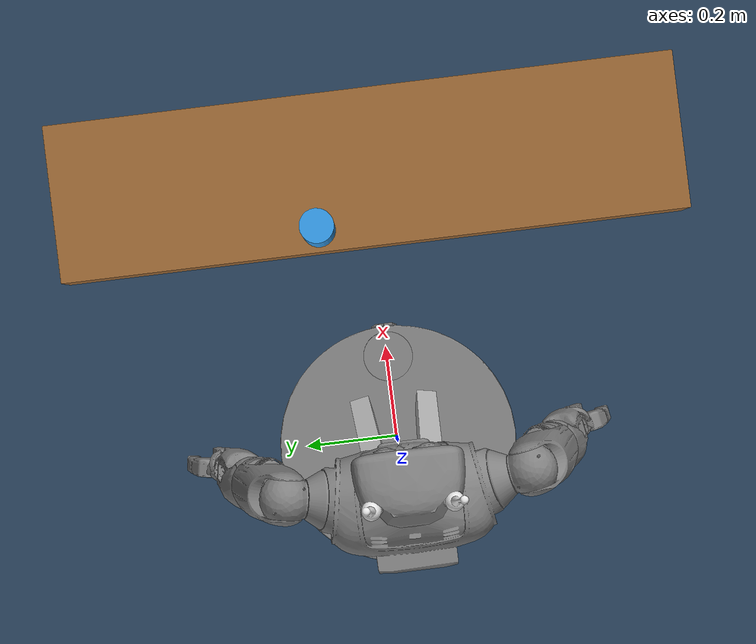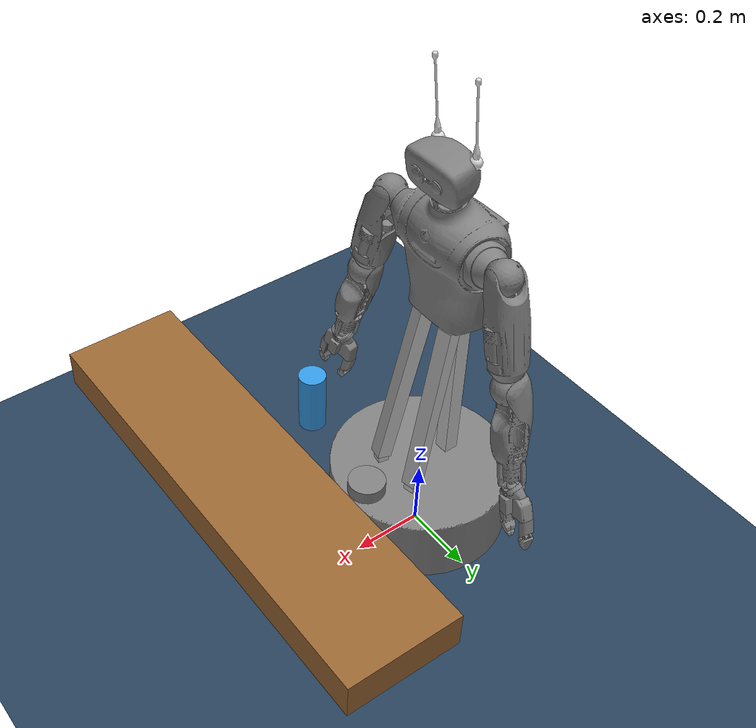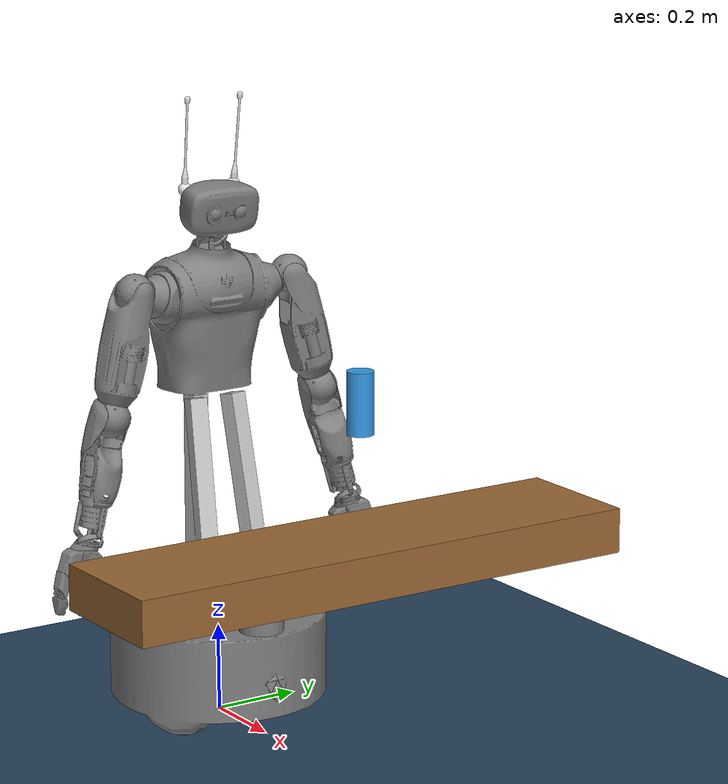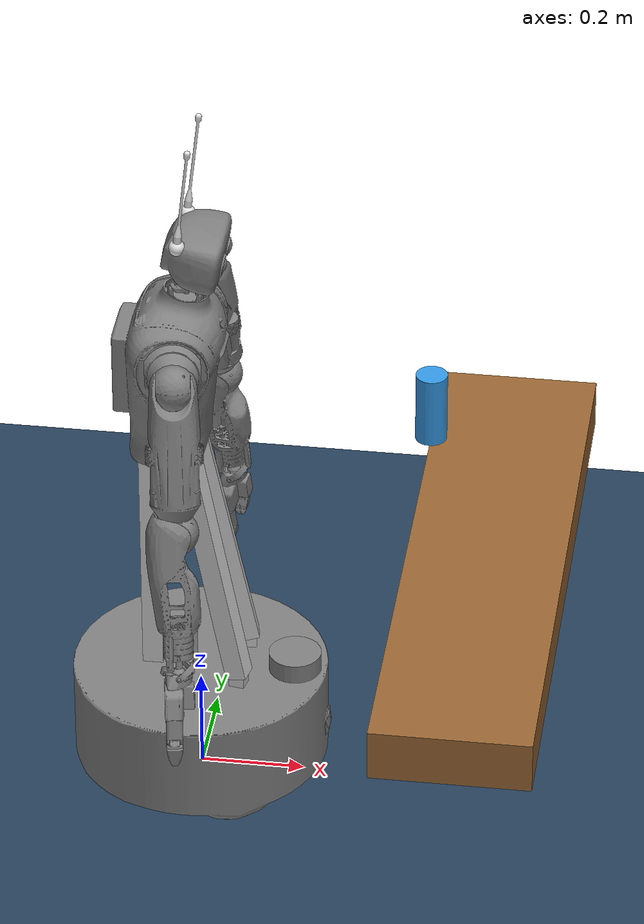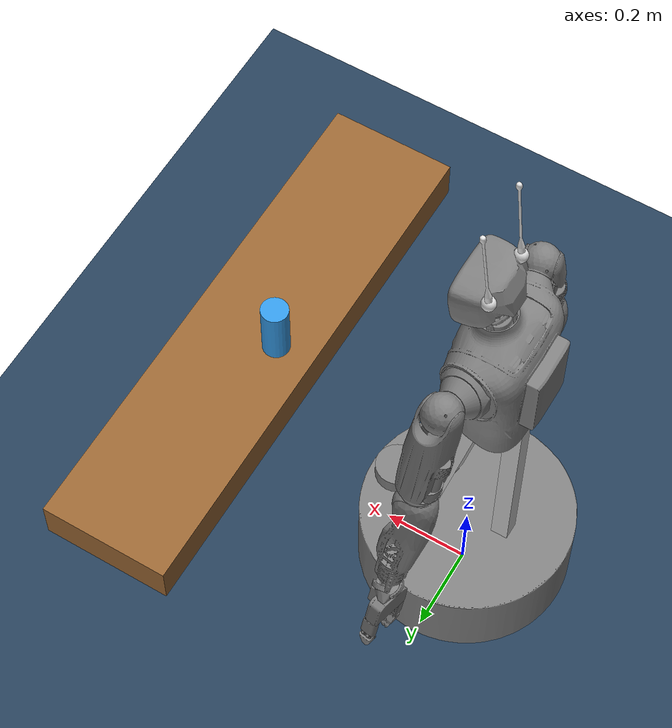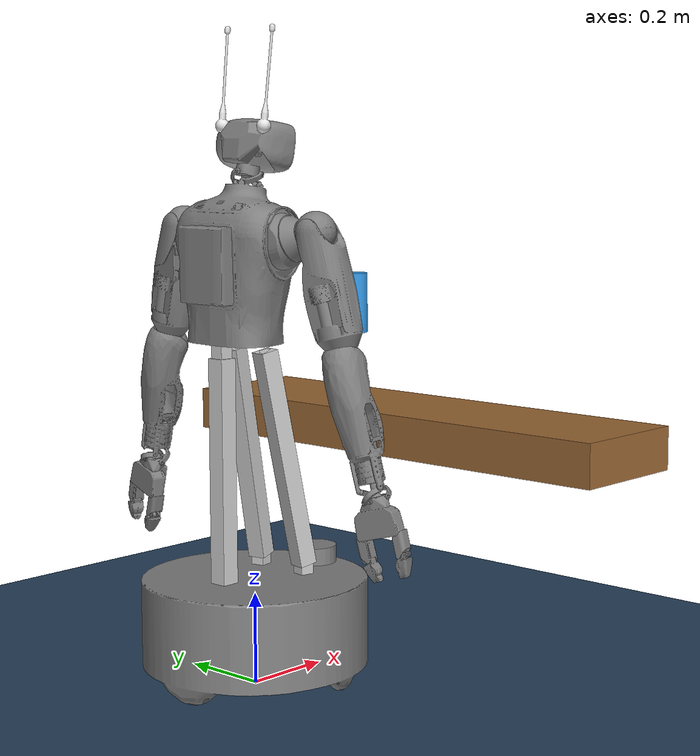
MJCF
<mujoco model="reachy2 scene">
	<compiler angle="radian"/>

	<option impratio="5">
		<flag multiccd="enable"/>
	</option>

	<include file="assets/reachy2_asset.xml" />

	<default>
		<geom friction="0.1 0.005 0.0001"/>
	</default>

	<visual>
		<headlight diffuse="0.6 0.6 0.6" ambient="0.3 0.3 0.3" specular="0 0 0" />
		<rgba haze="0.15 0.25 0.35 1" />
		<global azimuth="150" elevation="-20" />
	</visual>

	<asset>
		<texture type="skybox" builtin="gradient" rgb1="0.3 0.5 0.7" rgb2="0 0 0" width="512"
			height="3072" />
		<texture type="2d" name="groundplane" builtin="checker" mark="edge" rgb1="0.2 0.3 0.4"
			rgb2="0.1 0.2 0.3" markrgb="0.8 0.8 0.8" width="300" height="300" />
		<material name="groundplane" texture="groundplane" texuniform="true" texrepeat="5 5"
			reflectance="0.2" />
	</asset>

	<worldbody>
		<light pos="0 0 3" dir="0 0 -1" directional="false" />
		<body name="floor">
			<geom contype="1" conaffinity="2" friction=".1 0.005 0.0001" name="floor" pos="0 0 0"
				size="0 0 .25" type="plane" material="groundplane" condim="3"
				solimp="0 0.95 0.001 0.5 2" solref="0.02 1" margin="0"/>
		</body>

		<body name="reachy" pos="0 0 0" euler="0 0 0">
            <freejoint name="mobile_base" />
            <include file="objects/reachy2_body.xml"/>
        </body>

		<body>
			<geom name="table_top" type="box" pos="0.55 0 0.5" size="0.15 0.6 0.05"
				rgba="0.6 0.4 0.2 1"
				friction="3.0 0.01 0.002"
				condim="4"
				solref="0.005 1"
				solimp="0.98 0.98 0.001"
				contype="1" conaffinity="1" />
		</body>
		<!-- Table -->
				<!-- friction="3.0 0.01 0.002" -->
		<body name="bottle" pos="0.43 0.1 0.8">
		    <freejoint name="bottle_free"/>

			<geom name="bottle_main" type="cylinder" size="0.03 0.07"
				rgba="0.2 0.6 0.9 1"
				mass="0.8"
                friction="1.0 0.5 0.01"
				condim="6"
				solref="0.005 1"
				solimp="0.97 0.97 0.001"
				margin="0.002"
				contype="1" conaffinity="1"/>
		</body>

	</worldbody>

</mujoco>

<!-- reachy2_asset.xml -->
<mujocoinclude>
    <asset>
        <mesh name="mobile_base_visual" file="meshes/reachy2/mobile_base_visual.obj" />
        <mesh name="torso_visual" file="meshes/reachy2/torso_visual.obj" />
        <mesh name="torso_collider" file="meshes/reachy2/torso_collider.obj" />
        <mesh name="head_visual" file="meshes/reachy2/head_visual.obj" />
        <mesh name="head_collider" file="meshes/reachy2/head_collider.obj" />
        <mesh name="head_antenna_visual" file="meshes/reachy2/head_antenna_visual.obj" />
        <mesh name="2D_sphere_visual" file="meshes/reachy2/2D_sphere_visual.obj" />
        <mesh name="upper_arm_visual" file="meshes/reachy2/upper_arm_visual.obj" />
        <mesh name="upper_arm_collider" file="meshes/reachy2/upper_arm_collider.obj" />
        <mesh name="forearm_visual" file="meshes/reachy2/forearm_visual.obj" />
        <mesh name="forearm_collider" file="meshes/reachy2/forearm_collider.obj" />
        <mesh name="pincette_base_collider" file="meshes/reachy2/pincette_base_collider.obj" />
        <mesh name="pincette_base_visual" file="meshes/reachy2/pincette_base_visual.obj" />
        <mesh name="pincette_proximal_collider" file="meshes/reachy2/pincette_proximal_collider.obj" />
        <mesh name="pincette_proximal_visual" file="meshes/reachy2/pincette_proximal_visual.obj" />
        <mesh name="pincette_distal_collider" file="meshes/reachy2/pincette_distal_collider.obj" />
        <mesh name="pincette_distal" file="meshes/reachy2/pincette_distal.obj" />
        <texture builtin="checker" height="10" name="texplane" rgb1="0 0 0" rgb2="0.8 0.8 0.8" type="2d" width="10" />
        <material name="checkmat" reflectance="0.5" shininess="1" specular="1" texrepeat="6 6" texture="texplane" />

    </asset>

    <default>
        <!-- Modifications avant mujoco ok-->

        <!-- This looks good -->
        <joint damping="10" frictionloss="2.0" actuatorfrcrange="-2000 2000" armature="1.0"/>
        <position kp="500" kv="10" />

        <default class="gripper">
        <joint damping="0.1" frictionloss="1.0" actuatorfrcrange="-20 20" armature="1.0"/>
        <position kp="200" kv="0" />
        </default>

        <default class="tripod">
        <joint damping="1000" frictionloss="50.0" actuatorfrcrange="-2000000 2000000" />
        <position kp="50000" kv="1" />
        </default>

        <default class="wheel">
        <joint  armature="0.1" />
        </default>

        <default class="visual">
        <geom type="mesh" mass="0" group="2" contype="0" conaffinity="0"/>
        </default>
        <default class="collider">
        <geom group="3" type="mesh" condim="6" friction="1 5e-3 5e-4" solref=".01 1" contype="1"
            conaffinity="1" />
        </default>

        <default class="gripper_collider">
        <geom group="3" type="mesh" condim="6" friction="1.0 0.5 0.01" solref=".01 1" contype="1"
            conaffinity="1" />
        </default>

        <default class="gripper_collider_box">
        <geom group="3" type="box" friction="4.0 1.0 0.01" condim="6" contype="1" conaffinity="1"
            solimp="0.95 0.99 0.01" solref="0.002 1" margin="0.001"/>

        </default>

        <default class="wheel_collision">

        <geom friction="0.3 0.005 0.0001" condim="3" contype="2" conaffinity="0"
            solimp="0 0.95 0.001 0.5 2" solref="0.02 1" margin="0" />
        </default>

    </default>

    <equality>
        <joint
        joint1="r_hand_finger"
        joint2="r_hand_finger_proximal"
        polycoef="0.554 -0.4689 0 0 0"
        solimp="0.95 0.99 0.001"
        solref="0.005 1"
        />
        <joint
        joint1="r_hand_finger_proximal"
        joint2="r_hand_finger_distal"
        polycoef="0 -1 0 0 0"
        solimp="0.95 0.99 0.001"
        solref="0.005 1"
        />
        <joint
        joint1="r_hand_finger_proximal"
        joint2="r_hand_finger_proximal_mimic"
        polycoef="0 1 0 0 0"
        solimp="0.95 0.99 0.001"
        solref="0.005 1"
        />
        <joint
        joint1="r_hand_finger_distal"
        joint2="r_hand_finger_distal_mimic"
        polycoef="0 1 0 0 0"
        solimp="0.95 0.99 0.001"
        solref="0.005 1"
        />
        <joint
        joint1="l_hand_finger"
        joint2="l_hand_finger_proximal"
        polycoef="0.554 -0.4689 0 0 0"
        solimp="0.95 0.99 0.001"
        solref="0.005 1"
        />
        <joint
        joint1="l_hand_finger_proximal"
        joint2="l_hand_finger_distal"
        polycoef="0 -1 0 0 0"
        solimp="0.95 0.99 0.001"
        solref="0.005 1"
        />
        <joint
        joint1="l_hand_finger_proximal"
        joint2="l_hand_finger_proximal_mimic"
        polycoef="0 1 0 0 0"
        solimp="0.95 0.99 0.001"
        solref="0.005 1"
        />
        <joint
        joint1="l_hand_finger_distal"
        joint2="l_hand_finger_distal_mimic"
        polycoef="0 1 0 0 0"
        solimp="0.95 0.99 0.001"
        solref="0.005 1"
        />

        <!--     joint1="left_bar_joint_mimic" -->
        <!--     joint2="tripod_joint" -->
        <!--     polycoef="-0.20061291 0.40967047 -0.74428024 0.82037152 0" -->
        <!--     solimp="0.95 0.99 0.001" -->
        <!--     solref="0.005 1" -->

        <!--     joint1="tripod_joint" -->
        <!--     joint2="left_bar_prism_joint_mimic" -->
        <!--     polycoef="0.4814718126556904 -0.9861535348976198 0 0 0" -->
        <!--     solimp="0.95 0.99 0.001" -->
        <!--     solref="0.005 1" -->

        <!--     joint1="right_bar_joint_mimic" -->
        <!--     joint2="tripod_joint" -->
        <!--     polycoef="-0.20061291 0.40967047 -0.74428024 0.82037152 0" -->
        <!--     solimp="0.95 0.99 0.001" -->
        <!--     solref="0.005 1" -->
        <!--     joint1="tripod_joint" -->
        <!--     joint2="right_bar_prism_joint_mimic" -->
        <!--     polycoef="0.4814718126556904 -0.9861535348976198 0 0 0" -->
        <!--     solimp="0.95 0.99 0.001" -->
        <!--     solref="0.005 1" -->

        <joint
        joint1="left_bar_joint_mimic"
        joint2="tripod_joint"
        polycoef="0 0.40967047 -0.74428024 0.82037152 0"
        solimp="0.95 0.99 0.001"
        solref="0.005 1"
        />

        <joint
        joint1="tripod_joint"
        joint2="left_bar_prism_joint_mimic"
        polycoef="0 -0.9861535348976198 0 0 0"
        solimp="0.95 0.99 0.001"
        solref="0.005 1"
        />

        <joint
        joint1="right_bar_joint_mimic"
        joint2="tripod_joint"
        polycoef="0 0.40967047 -0.74428024 0.82037152 0"
        solimp="0.95 0.99 0.001"
        solref="0.005 1"
        />
        <joint
        joint1="tripod_joint"
        joint2="right_bar_prism_joint_mimic"
        polycoef="0 -0.9861535348976198 0 0 0"
        solimp="0.95 0.99 0.001"
        solref="0.005 1"
        />

    </equality>
    <actuator>
        <position name="tripod_joint" joint="tripod_joint" gear="1" inheritrange="1" class="tripod" />

        <position name="neck_roll" joint="neck_roll" gear="1" inheritrange="1" />
        <position name="neck_pitch" joint="neck_pitch" gear="1" inheritrange="1" />
        <position name="neck_yaw" joint="neck_yaw" gear="1" inheritrange="1" />

        <position name="antenna_left" joint="antenna_left" gear="1" inheritrange="1" />
        <position name="antenna_right" joint="antenna_right" gear="1" inheritrange="1" />

        <position
        name="l_shoulder_pitch"
        joint="l_shoulder_pitch"
        gear="1"
        inheritrange="1"
        />
        <position
        name="l_shoulder_roll"
        joint="l_shoulder_roll"
        gear="1"
        inheritrange="1"
        />
        <position
        name="l_elbow_yaw"
        joint="l_elbow_yaw"
        gear="1"
        inheritrange="1"
        />
        <position
        name="l_elbow_pitch"
        joint="l_elbow_pitch"
        gear="1"
        inheritrange="1"
        />
        <position
        name="l_wrist_roll"
        joint="l_wrist_roll"
        gear="1"
        inheritrange="1"
        />
        <position
        name="l_wrist_pitch"
        joint="l_wrist_pitch"
        gear="1"
        inheritrange="1"
        />
        <position
        name="l_wrist_yaw"
        joint="l_wrist_yaw"
        gear="1"
        inheritrange="1"
        />
        <position
        name="r_shoulder_pitch"
        joint="r_shoulder_pitch"
        gear="1"
        inheritrange="1"
        />
        <position
        name="r_shoulder_roll"
        joint="r_shoulder_roll"
        gear="1"
        inheritrange="1"
        />
        <position
        name="r_elbow_yaw"
        joint="r_elbow_yaw"
        gear="1"
        inheritrange="1"
        />
        <position
        name="r_elbow_pitch"
        joint="r_elbow_pitch"
        gear="1"
        inheritrange="1"
        />
        <position
        name="r_wrist_roll"
        joint="r_wrist_roll"
        gear="1"
        inheritrange="1"
        />
        <position
        name="r_wrist_pitch"
        joint="r_wrist_pitch"
        gear="1"
        inheritrange="1"
        />
        <position
        name="r_wrist_yaw"
        joint="r_wrist_yaw"
        gear="1"
        inheritrange="1"
        />
        <position
        name="r_hand_finger"
        joint="r_hand_finger"
        gear="1"
        inheritrange="1"
        class="gripper"
        />
        <position
        name="l_hand_finger"
        joint="l_hand_finger"
        gear="1"
        inheritrange="1"
        class="gripper"
        />

        <!--     name="drivewhl2_joint" -->
        <!--     joint="drivewhl2_joint" -->
        <!--     ctrlrange="-5 5" kv="100" -->
        <!--     name="drivewhl1_joint" -->
        <!--     joint="drivewhl1_joint" -->
        <!--     ctrlrange="-5 5" kv="100" -->
        <!--     name="drivewhl3_joint" -->
        <!--     joint="drivewhl3_joint" -->
        <!--     ctrlrange="-5 5" kv="100" -->

        <!--     name="drivewhl2_joint" -->
        <!--     joint="drivewhl2_joint" -->
        <!--     ctrlrange="-5 5" kv="1000" -->
        <!--     name="drivewhl1_joint" -->
        <!--     joint="drivewhl1_joint" -->
        <!--     ctrlrange="-5 5" kv="1000" -->
        <!--     name="drivewhl3_joint" -->
        <!--     joint="drivewhl3_joint" -->
        <!--     ctrlrange="-5 5" kv="1000" -->

        <motor
        name="drivewhl2_joint"
        joint="drivewhl2_joint"
        ctrlrange="-50 50" ctrllimited="true"
        />
        <motor
        name="drivewhl1_joint"
        joint="drivewhl1_joint"
        ctrlrange="-50 50" ctrllimited="true"
        />
        <motor
        name="drivewhl3_joint"
        joint="drivewhl3_joint"
        ctrlrange="-50 50" ctrllimited="true"
        />

        <!--     name="drivewhl2_joint" -->
        <!--     joint="drivewhl2_joint" -->
        <!--     name="drivewhl1_joint" -->
        <!--     joint="drivewhl1_joint" -->
        <!--     name="drivewhl3_joint" -->
        <!--     joint="drivewhl3_joint" -->

    </actuator>

    <contact>
        <exclude name="torso_r_shoulder" body1="torso" body2="r_elbow_arm_link" />
        <exclude name="torso_l_shoulder" body1="torso" body2="l_elbow_arm_link" />

        <exclude name="l_arm_forearm" body1="l_elbow_arm_link" body2="l_elbow_forearm_link" />
        <exclude name="r_arm_forearm" body1="r_elbow_arm_link" body2="r_elbow_forearm_link" />

        <exclude name="l_forearm_gripper" body1="l_elbow_forearm_link" body2="l_hand_palm_link" />
        <exclude name="r_forearm_gripper" body1="r_elbow_forearm_link" body2="r_hand_palm_link" />

        <exclude name="back_bar" body1="back_bar_base" body2="back_bar_inner" />

    </contact>

</mujocoinclude>

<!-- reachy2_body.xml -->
<mujocoinclude>
    <body name="reachy_body">
        <inertial pos="0.008 -0.00048 0.112" quat="-0.0363977 0.704069 0.0372966 0.708217" mass="24"
            diaginertia="0.709918 0.423857 0.407726" />
        <geom type="mesh" mesh="mobile_base_visual" class="visual" friction="5 0.1 0.01"/>
        <geom size="0.245 0.095" pos="0 0 0.145" type="cylinder" class="collider" />
        <body name="drivewhl1_link" pos="0.099 -0.171473 0.105" quat="0.965926 0 0 0.258819">
            <inertial pos="0 0 0" quat="0.5 0.5 -0.5 0.5" mass="0.5"
            diaginertia="0.00275625 0.00142917 0.00142917"/>
            <joint name="right_wheel" pos="0 0 0" axis="0 1 0" class="wheel" />

            <geom size="0.105 0.105 0.0175" quat="0.707107 0.707107 0 0" type="ellipsoid" class="visual" />
            <body pos="0.0 0.0 0.0945" euler="0 0 0">
            <inertial pos="0 0 0.0" quat="1 0 0 0" mass="0.01" diaginertia="0.0001 0.0001 0.0001" />
            <geom size="0.0105 0.0105 0.04" quat="0.707107 0 0.707107  0" type="ellipsoid"
                material="checkmat" class="visual" />
            <geom size="0.0105 0.0105 0.04" quat="0.707107 0 0.707107  0" type="ellipsoid"
                class="wheel_collision" />
            <joint pos="0 0 0" axis="1 0 0" />
            </body>

            <body pos="0.0 0.0 -0.0945" euler="0 0 0">
            <inertial pos="0 0 0.0" quat="1 0 0 0" mass="0.01" diaginertia="0.0001 0.0001 0.0001" />
            <geom size="0.0105 0.0105 0.04" quat="0.707107 0 0.707107  0" type="ellipsoid"
                material="checkmat" class="visual" />
            <geom size="0.0105 0.0105 0.04" quat="0.707107 0 0.707107  0" type="ellipsoid"
                class="wheel_collision" />
            <joint pos="0 0 0" axis="1 0 0" />
            </body>

            <body pos="0.0945 0.0 0.0" euler="0 1.5707963267948966 0">
            <inertial pos="0 0 0.0" quat="1 0 0 0" mass="0.01" diaginertia="0.0001 0.0001 0.0001" />
            <geom size="0.0105 0.0105 0.04" quat="0.707107 0 0.707107  0" type="ellipsoid"
                material="checkmat" class="visual" />
            <geom size="0.0105 0.0105 0.04" quat="0.707107 0 0.707107  0" type="ellipsoid"
                class="wheel_collision" />
            <joint pos="0 0 0" axis="1 0 0" />
            </body>

            <body pos="-0.0945 0.0 0.0" euler="0 1.5707963267948966 0">
            <inertial pos="0 0 0.0" quat="1 0 0 0" mass="0.01" diaginertia="0.0001 0.0001 0.0001" />
            <geom size="0.0105 0.0105 0.04" quat="0.707107 0 0.707107  0" type="ellipsoid"
                material="checkmat" class="visual" />
            <geom size="0.0105 0.0105 0.04" quat="0.707107 0 0.707107  0" type="ellipsoid"
                class="wheel_collision" />
            <joint pos="0 0 0" axis="1 0 0" />
            </body>

            <body pos="0.06682159082212874 0.0 0.06682159082212874" euler="0 0.7853981633974483 0">
            <inertial pos="0 0 0.0" quat="1 0 0 0" mass="0.01" diaginertia="0.0001 0.0001 0.0001" />
            <geom size="0.0105 0.0105 0.04" quat="0.707107 0 0.707107  0" type="ellipsoid"
                material="checkmat" class="visual" />
            <geom size="0.0105 0.0105 0.04" quat="0.707107 0 0.707107  0" type="ellipsoid"
                class="wheel_collision" />
            <joint pos="0 0 0" axis="1 0 0" />
            </body>

            <body pos="-0.06682159082212874 0.0 0.06682159082212874" euler="0 -0.7853981633974483 0">
            <inertial pos="0 0 0.0" quat="1 0 0 0" mass="0.01" diaginertia="0.0001 0.0001 0.0001" />
            <geom size="0.0105 0.0105 0.04" quat="0.707107 0 0.707107  0" type="ellipsoid"
                material="checkmat" class="visual" />
            <geom size="0.0105 0.0105 0.04" quat="0.707107 0 0.707107  0" type="ellipsoid"
                class="wheel_collision" />
            <joint pos="0 0 0" axis="1 0 0" />
            </body>

            <body pos="-0.06682159082212874 0.0 -0.06682159082212874" euler="0 0.7853981633974483 0">
            <inertial pos="0 0 0.0" quat="1 0 0 0" mass="0.01" diaginertia="0.0001 0.0001 0.0001" />
            <geom size="0.0105 0.0105 0.04" quat="0.707107 0 0.707107  0" type="ellipsoid"
                material="checkmat" class="visual" />
            <geom size="0.0105 0.0105 0.04" quat="0.707107 0 0.707107  0" type="ellipsoid"
                class="wheel_collision" />
            <joint pos="0 0 0" axis="1 0 0" />
            </body>

            <body pos="0.06682159082212874 0.0 -0.06682159082212874" euler="0 -0.7853981633974483 0">
            <inertial pos="0 0 0.0" quat="1 0 0 0" mass="0.01" diaginertia="0.0001 0.0001 0.0001" />
            <geom size="0.0105 0.0105 0.04" quat="0.707107 0 0.707107  0" type="ellipsoid"
                material="checkmat" class="visual" />
            <geom size="0.0105 0.0105 0.04" quat="0.707107 0 0.707107  0" type="ellipsoid"
                class="wheel_collision" />
            <joint pos="0 0 0" axis="1 0 0" />
            </body>

        </body>
        <body name="drivewhl2_link" pos="0.099 0.171473 0.105" quat="-0.258819 0 0 -0.965926">
            <inertial pos="0 0 0" quat="0.5 0.5 -0.5 0.5" mass="0.5"
            diaginertia="0.00275625 0.00142917 0.00142917" />
            <joint name="left_wheel" pos="0 0 0" axis="0 1 0" class="wheel" />

            <geom size="0.105 0.105 0.0175" quat="0.707107 0.707107 0 0" type="ellipsoid" class="visual" />

            <body pos="0.0 0.0 0.0945" euler="0 0 0">
            <inertial pos="0 0 0.0" quat="1 0 0 0" mass="0.01" diaginertia="0.0001 0.0001 0.0001" />
            <geom size="0.0105 0.0105 0.04" quat="0.707107 0 0.707107  0" type="ellipsoid"
                material="checkmat" class="visual" />
            <geom size="0.0105 0.0105 0.04" quat="0.707107 0 0.707107  0" type="ellipsoid"
                class="wheel_collision" />
            <joint pos="0 0 0" axis="1 0 0" />
            </body>

            <body pos="0.0 0.0 -0.0945" euler="0 0 0">
            <inertial pos="0 0 0.0" quat="1 0 0 0" mass="0.01" diaginertia="0.0001 0.0001 0.0001" />
            <geom size="0.0105 0.0105 0.04" quat="0.707107 0 0.707107  0" type="ellipsoid"
                material="checkmat" class="visual" />
            <geom size="0.0105 0.0105 0.04" quat="0.707107 0 0.707107  0" type="ellipsoid"
                class="wheel_collision" />
            <joint pos="0 0 0" axis="1 0 0" />
            </body>

            <body pos="0.0945 0.0 0.0" euler="0 1.5707963267948966 0">
            <inertial pos="0 0 0.0" quat="1 0 0 0" mass="0.01" diaginertia="0.0001 0.0001 0.0001" />
            <geom size="0.0105 0.0105 0.04" quat="0.707107 0 0.707107  0" type="ellipsoid"
                material="checkmat" class="visual" />
            <geom size="0.0105 0.0105 0.04" quat="0.707107 0 0.707107  0" type="ellipsoid"
                class="wheel_collision" />
            <joint pos="0 0 0" axis="1 0 0" />
            </body>

            <body pos="-0.0945 0.0 0.0" euler="0 1.5707963267948966 0">
            <inertial pos="0 0 0.0" quat="1 0 0 0" mass="0.01" diaginertia="0.0001 0.0001 0.0001" />
            <geom size="0.0105 0.0105 0.04" quat="0.707107 0 0.707107  0" type="ellipsoid"
                material="checkmat" class="visual" />
            <geom size="0.0105 0.0105 0.04" quat="0.707107 0 0.707107  0" type="ellipsoid"
                class="wheel_collision" />
            <joint pos="0 0 0" axis="1 0 0" />
            </body>

            <body pos="0.06682159082212874 0.0 0.06682159082212874" euler="0 0.7853981633974483 0">
            <inertial pos="0 0 0.0" quat="1 0 0 0" mass="0.01" diaginertia="0.0001 0.0001 0.0001" />
            <geom size="0.0105 0.0105 0.04" quat="0.707107 0 0.707107  0" type="ellipsoid"
                material="checkmat" class="visual" />
            <geom size="0.0105 0.0105 0.04" quat="0.707107 0 0.707107  0" type="ellipsoid"
                class="wheel_collision" />
            <joint pos="0 0 0" axis="1 0 0" />
            </body>

            <body pos="-0.06682159082212874 0.0 0.06682159082212874" euler="0 -0.7853981633974483 0">
            <inertial pos="0 0 0.0" quat="1 0 0 0" mass="0.01" diaginertia="0.0001 0.0001 0.0001" />
            <geom size="0.0105 0.0105 0.04" quat="0.707107 0 0.707107  0" type="ellipsoid"
                material="checkmat" class="visual" />
            <geom size="0.0105 0.0105 0.04" quat="0.707107 0 0.707107  0" type="ellipsoid"
                class="wheel_collision" />
            <joint pos="0 0 0" axis="1 0 0" />
            </body>

            <body pos="-0.06682159082212874 0.0 -0.06682159082212874" euler="0 0.7853981633974483 0">
            <inertial pos="0 0 0.0" quat="1 0 0 0" mass="0.01" diaginertia="0.0001 0.0001 0.0001" />
            <geom size="0.0105 0.0105 0.04" quat="0.707107 0 0.707107  0" type="ellipsoid"
                material="checkmat" class="visual" />
            <geom size="0.0105 0.0105 0.04" quat="0.707107 0 0.707107  0" type="ellipsoid"
                class="wheel_collision" />
            <joint pos="0 0 0" axis="1 0 0" />
            </body>

            <body pos="0.06682159082212874 0.0 -0.06682159082212874" euler="0 -0.7853981633974483 0">
            <inertial pos="0 0 0.0" quat="1 0 0 0" mass="0.01" diaginertia="0.0001 0.0001 0.0001" />
            <geom size="0.0105 0.0105 0.04" quat="0.707107 0 0.707107  0" type="ellipsoid"
                material="checkmat" class="visual" />
            <geom size="0.0105 0.0105 0.04" quat="0.707107 0 0.707107  0" type="ellipsoid"
                class="wheel_collision" />
            <joint pos="0 0 0" axis="1 0 0" />
            </body>

        </body>
        <body name="drivewhl3_link" pos="-0.198 0 0.105" quat="0.707107 0 0 -0.707107">
            <inertial pos="0 0 0" quat="0.5 0.5 -0.5 0.5" mass="0.5"
            diaginertia="0.00275625 0.00142917 0.00142917" />
            <joint name="back_wheel" pos="0 0 0" axis="0 1 0" class="wheel" />

            <geom size="0.105 0.105 0.0175" quat="0.707107 0.707107 0 0" type="ellipsoid" class="visual" />

            <body pos="0.0 0.0 0.0945" euler="0 0 0">
            <inertial pos="0 0 0.0" quat="1 0 0 0" mass="0.01" diaginertia="0.0001 0.0001 0.0001" />
            <geom size="0.0105 0.0105 0.04" quat="0.707107 0 0.707107  0" type="ellipsoid"
                material="checkmat" class="visual" />
            <geom size="0.0105 0.0105 0.04" quat="0.707107 0 0.707107  0" type="ellipsoid"
                class="wheel_collision" />
            <joint pos="0 0 0" axis="1 0 0" />
            </body>

            <body pos="0.0 0.0 -0.0945" euler="0 0 0">
            <inertial pos="0 0 0.0" quat="1 0 0 0" mass="0.01" diaginertia="0.0001 0.0001 0.0001" />
            <geom size="0.0105 0.0105 0.04" quat="0.707107 0 0.707107  0" type="ellipsoid"
                material="checkmat" class="visual" />
            <geom size="0.0105 0.0105 0.04" quat="0.707107 0 0.707107  0" type="ellipsoid"
                class="wheel_collision" />
            <joint pos="0 0 0" axis="1 0 0" />
            </body>

            <body pos="0.0945 0.0 0.0" euler="0 1.5707963267948966 0">
            <inertial pos="0 0 0.0" quat="1 0 0 0" mass="0.01" diaginertia="0.0001 0.0001 0.0001" />
            <geom size="0.0105 0.0105 0.04" quat="0.707107 0 0.707107  0" type="ellipsoid"
                material="checkmat" class="visual" />
            <geom size="0.0105 0.0105 0.04" quat="0.707107 0 0.707107  0" type="ellipsoid"
                class="wheel_collision" />
            <joint pos="0 0 0" axis="1 0 0" />
            </body>

            <body pos="-0.0945 0.0 0.0" euler="0 1.5707963267948966 0">
            <inertial pos="0 0 0.0" quat="1 0 0 0" mass="0.01" diaginertia="0.0001 0.0001 0.0001" />
            <geom size="0.0105 0.0105 0.04" quat="0.707107 0 0.707107  0" type="ellipsoid"
                material="checkmat" class="visual" />
            <geom size="0.0105 0.0105 0.04" quat="0.707107 0 0.707107  0" type="ellipsoid"
                class="wheel_collision" />
            <joint pos="0 0 0" axis="1 0 0" />
            </body>

            <body pos="0.06682159082212874 0.0 0.06682159082212874" euler="0 0.7853981633974483 0">
            <inertial pos="0 0 0.0" quat="1 0 0 0" mass="0.01" diaginertia="0.0001 0.0001 0.0001" />
            <geom size="0.0105 0.0105 0.04" quat="0.707107 0 0.707107  0" type="ellipsoid"
                material="checkmat" class="visual" />
            <geom size="0.0105 0.0105 0.04" quat="0.707107 0 0.707107  0" type="ellipsoid"
                class="wheel_collision" />
            <joint pos="0 0 0" axis="1 0 0" />
            </body>

            <body pos="-0.06682159082212874 0.0 0.06682159082212874" euler="0 -0.7853981633974483 0">
            <inertial pos="0 0 0.0" quat="1 0 0 0" mass="0.01" diaginertia="0.0001 0.0001 0.0001" />
            <geom size="0.0105 0.0105 0.04" quat="0.707107 0 0.707107  0" type="ellipsoid"
                material="checkmat" class="visual" />
            <geom size="0.0105 0.0105 0.04" quat="0.707107 0 0.707107  0" type="ellipsoid"
                class="wheel_collision" />
            <joint pos="0 0 0" axis="1 0 0" />
            </body>

            <body pos="-0.06682159082212874 0.0 -0.06682159082212874" euler="0 0.7853981633974483 0">
            <inertial pos="0 0 0.0" quat="1 0 0 0" mass="0.01" diaginertia="0.0001 0.0001 0.0001" />
            <geom size="0.0105 0.0105 0.04" quat="0.707107 0 0.707107  0" type="ellipsoid"
                material="checkmat" class="visual" />
            <geom size="0.0105 0.0105 0.04" quat="0.707107 0 0.707107  0" type="ellipsoid"
                class="wheel_collision" />
            <joint pos="0 0 0" axis="1 0 0" />
            </body>

            <body pos="0.06682159082212874 0.0 -0.06682159082212874" euler="0 -0.7853981633974483 0">
            <inertial pos="0 0 0.0" quat="1 0 0 0" mass="0.01" diaginertia="0.0001 0.0001 0.0001" />
            <geom size="0.0105 0.0105 0.04" quat="0.707107 0 0.707107  0" type="ellipsoid"
                material="checkmat" class="visual" />
            <geom size="0.0105 0.0105 0.04" quat="0.707107 0 0.707107  0" type="ellipsoid"
                class="wheel_collision" />
            <joint pos="0 0 0" axis="1 0 0" />
            </body>

        </body>
        <body name="lidar_link" pos="0.184 0 0.25" quat="0 0 0 1">
            <inertial pos="0 0 0" mass="0.125" diaginertia="0.001 0.001 0.001" />
            <geom size="0.0508 0.0275" type="cylinder" />
        </body>
        <body name="back_bar_base" pos="-0.09 0 0.241">
            <inertial pos="0 0 0" mass="0.759" diaginertia="0.0002024 0.0002024 0.0002024" />
            <geom size="0.025 0.025 0.2425" pos="0 0 0.2425" type="box" rgba="0.8 0.8 0.8 1"
            class="collider" />
            <geom size="0.02 0.02 0.2425" pos="0 0 0.2425" type="box" rgba="0.8 0.8 0.8 1"
            class="visual" />

            <body name="back_bar_inner" pos="0 0 0.035">
            <inertial pos="0 0 0" mass="0.759" diaginertia="0.0002024 0.0002024 0.0002024" />
            <joint name="tripod_joint" pos="0 0 0" axis="0 0 1" type="slide" range="0 0.21"
                class="tripod" />
            <geom size="0.025 0.025 0.2425" pos="0 0 0.2425" type="box" rgba="0.8 0.8 0.8 1"
                class="collider" />
            <geom size="0.015 0.015 0.2425" pos="0 0 0.2425" type="box" rgba="0.8 0.8 0.8 1"
                class="visual" />
            <body name="torso" pos="0.08 0 0.72">
                <site name="torso" pos="0.0 0.0 0 " />
                <inertial pos="-0.051614 -0.000471 -0.018363"
                quat="0.708121 0.704566 0.0268143 -0.0378516" mass="6.314"
                diaginertia="0.0741454 0.0547883 0.0445377" />
                <geom type="mesh" mesh="torso_visual" class="visual" />
                <geom type="mesh" mesh="torso_collider" class="collider" />

                <body name="left_bar_inner" pos="0 0.048 -0.258"
                quat="0.99046537  0.00952377 -0.09948142  0.09482141">

                <inertial pos="0 0 0" mass="0.759" diaginertia="0.0002024 0.0002024 0.0002024" />
                <joint name="left_bar_joint_mimic" pos="0 0 0" axis="0 1 0" />
                <geom size="0.015 0.015 0.2425" pos="0 0 -0.2425" type="box" density="0"
                    rgba="0.8 0.8 0.8 1" class="visual" />
                <geom size="0.025 0.025 0.2425" pos="0 0 -0.2425" type="box" rgba="0.8 0.8 0.8 1"
                    class="collider" />
                <body name="left_bar_base" pos="0 0 0">

                    <inertial pos="0 0 0" mass="1.759" diaginertia="0.000469067 0.000469067 0.000469067" />
                    <joint name="left_bar_prism_joint_mimic" pos="0 0 0" axis="0 0 1" type="slide" />
                    <geom size="0.02 0.02 0.2425" pos="0 0 -0.2425" type="box" rgba="0.8 0.8 0.8 1"
                    class="visual" />
                    <geom size="0.025 0.025 0.2425" pos="0 0 -0.2425" type="box" rgba="0.8 0.8 0.8 1"
                    class="collider" />
                </body>
                </body>
                <body name="right_bar_inner" pos="0 -0.048 -0.258"
                quat="0.99046537 -0.00952377 -0.09948142 -0.09482141">

                <inertial pos="0 0 0" mass="0.759" diaginertia="0.0002024 0.0002024 0.0002024" />
                <joint name="right_bar_joint_mimic" pos="0 0 0" axis="0 1 0" range="-1 1"
                    actuatorfrcrange="-0.01 0.01" />
                <geom size="0.015 0.015 0.2425" pos="0 0 -0.2425" type="box" rgba="0.8 0.8 0.8 1"
                    class="visual" />
                <geom size="0.025 0.025 0.2425" pos="0 0 -0.2425" type="box" rgba="0.8 0.8 0.8 1"
                    class="collider" />
                <body name="right_bar_base" pos="0 0 0">

                    <inertial pos="0 0 0" mass="1.759" diaginertia="0.000469067 0.000469067 0.000469067" />
                    <joint name="right_bar_prism_joint_mimic" pos="0 0 0" axis="0 0 1" type="slide" />
                    <geom size="0.02 0.02 0.2425" pos="0 0 -0.2425" type="box" rgba="0.8 0.8 0.8 1"
                    class="visual" />
                    <geom size="0.025 0.025 0.2425" pos="0 0 -0.2425" type="box" rgba="0.8 0.8 0.8 1"
                    class="collider" />
                </body>
                </body>

                <body name="neck_base_link" pos="0 0 0.115" quat="0.996195 0 0.0871557 0">
                <inertial pos="0 0 0" quat="0.820473 0.339851 -0.17592 0.424708" mass="0.001"
                    diaginertia="1.02e-06 9.9e-07 9.9e-07" />
                <body name="neck_dummy_link1">
                    <inertial pos="0 0 0" quat="0.5 0.5 -0.5 0.5" mass="0.005"
                    diaginertia="3e-06 2.54167e-06 2.54167e-06" />
                    <joint name="neck_roll" pos="0 0 0" axis="1 0 0" range="-0.35 0.35"
                    actuatorfrcrange="-50 50" />
                    <body name="neck_dummy_link2">
                    <inertial pos="0 0 0" quat="0.5 0.5 -0.5 0.5" mass="0.005"
                        diaginertia="3e-06 2.54167e-06 2.54167e-06" />
                    <joint name="neck_pitch" pos="0 0 0" axis="0 1 0" range="-0.35 0.35"
                        actuatorfrcrange="-50 50" />
                    <body name="neck_link">
                        <inertial pos="0 0 -0.025" quat="0.5 0.5 -0.5 0.5" mass="0.49"
                        diaginertia="0.000294 0.000249083 0.000249083" />
                        <joint name="neck_yaw" pos="0 0 0" axis="0 0 1" range="-1.57 1.57"
                        actuatorfrcrange="-50 50" />
                        <body name="neck_ball_link">
                        <inertial pos="0 0 0" quat="0.820473 0.339851 -0.17592 0.424708" mass="0.001"
                            diaginertia="1.02e-06 9.9e-07 9.9e-07" />
                        <body name="neck_out_link">
                            <inertial pos="0 0 0" quat="0.820473 0.339851 -0.17592 0.424708"
                            mass="0.001" diaginertia="1.02e-06 9.9e-07 9.9e-07" />
                            <body name="head">
                            <inertial pos="0.0116978 -0.00022144 0.0611705"
                                quat="0.552073 0.545887 -0.44927 0.442017" mass="0.325"
                                diaginertia="0.000897058 0.000850732 0.00063132" />
                            <geom type="mesh" mesh="head_visual" class="visual" />
                            <geom type="mesh" mesh="head_collider" class="collider" />
                            <body name="head_base">
                                <inertial pos="0 0 0" quat="0.820473 0.339851 -0.17592 0.424708"
                                mass="0.001" diaginertia="1.02e-06 9.9e-07 9.9e-07" />
                            </body>
                            <body name="head_tip" pos="0.05643 0 0.062">
                                <inertial pos="0 0 0" quat="0.820473 0.339851 -0.17592 0.424708"
                                mass="0.001" diaginertia="1.02e-06 9.9e-07 9.9e-07" />
                            </body>
                            <body name="antenna_left_link" pos="-0.023 0.055 0.091"
                                quat="0.764621 -0.215383 -0.45869 -0.398207">
                                <inertial pos="0 0 0" quat="0.820473 0.339851 -0.17592 0.424708"
                                mass="0.001" diaginertia="1.02e-06 9.9e-07 9.9e-07" />
                                <joint name="antenna_left" pos="0 0 0" axis="0 0 1"
                                range="-1.5708 1.5708" />
                                <geom type="mesh" rgba="0.9 0.9 0.9 1" mesh="head_antenna_visual"
                                class="visual" />
                            </body>
                            <body name="antenna_right_link" pos="-0.023 -0.055 0.091"
                                quat="0.764621 0.215383 -0.45869 0.398207">
                                <inertial pos="0 0 0" quat="0.820473 0.339851 -0.17592 0.424708"
                                mass="0.001" diaginertia="1.02e-06 9.9e-07 9.9e-07" />
                                <joint name="antenna_right" pos="0 0 0" axis="0 0 1"
                                range="-1.5708 1.5708" />
                                <geom type="mesh" rgba="0.9 0.9 0.9 1" mesh="head_antenna_visual"
                                class="visual" />
                            </body>
                            <body name="left_camera" pos="0.03531 0.0325 0.062">
                                <body name="left_camera_optical" quat="-0.5 -0.5 0.5 0.5">

                                <camera name="left_camera" pos="0 0 0" euler="0 0 0" fovy="58"
                                    mode="fixed"
                                    resolution="640 480" />
                                </body>

                            </body>
                            <body name="right_camera" pos="0.03531 -0.0325 0.062">
                                <body name="right_camera_optical" quat="-0.5 -0.5 0.5 0.5">
                                <camera name="right_camera" pos="0 0 0" euler="0 0 0" fovy="58"
                                    mode="fixed"
                                    resolution="640 480" />
                                </body>
                            </body>
                            <body name="tof_camera" pos="0.05643 0 0.061954">
                                <body name="tof_camera_optical" quat="-0.5 -0.5 0.5 0.5">
                                <camera name="tof_camera" pos="0 0 0" euler="0 0 0" fovy="58"
                                    mode="fixed"
                                    resolution="640 480" />
                                </body>
                            </body>
                            </body>
                        </body>
                        </body>
                    </body>
                    </body>
                </body>
                </body>
                <body name="r_shoulder_base_link" pos="0 -0.2 0"
                quat="0.790334 0.606445 0.0530571 0.0691453">
                <inertial pos="0 0 0" quat="0.820473 0.339851 -0.17592 0.424708" mass="0.001"
                    diaginertia="1.02e-06 9.9e-07 9.9e-07" />
                <body name="r_shoulder_dummy_link1">
                    <inertial pos="0 0 0" quat="0.820473 0.339851 -0.17592 0.424708" mass="0.001"
                    diaginertia="1.02e-06 9.9e-07 9.9e-07" />
                    <body name="r_shoulder_dummy_link2" quat="0.707107 -0.707107 0 0">
                    <inertial pos="0 0 0" quat="0.820473 0.339851 -0.17592 0.424708" mass="0.001"
                        diaginertia="1.02e-06 9.9e-07 9.9e-07" />
                    <body name="r_shoulder_first_link">
                        <inertial pos="9.6e-05 -1.5e-05 -0.01777"
                        quat="0.996708 0.000282525 0.00106617 -0.0810711" mass="0.487"
                        diaginertia="0.000578016 0.000572943 0.000243342" />
                        <joint name="r_shoulder_pitch" pos="0 0 0" axis="0 1 0" range="-3.14159 3.14159"
                        actuatorfrcrange="-50 50" />
                        <geom quat="0.707107 0.707107 0 0" mesh="2D_sphere_visual" class="visual" />
                        <body name="r_shoulder_ball_link">
                        <inertial pos="0 0 0" quat="0.820473 0.339851 -0.17592 0.424708" mass="0.001"
                            diaginertia="1.02e-06 9.9e-07 9.9e-07" />
                        <joint name="r_shoulder_roll" pos="0 0 0" axis="1 0 0" range="-3.14159 0"
                            actuatorfrcrange="-50 50" />
                        <body name="r_shoulder_fix_link" quat="0.707107 0.707107 0 0">
                            <inertial pos="0 0 0" quat="0.820473 0.339851 -0.17592 0.424708"
                            mass="0.001" diaginertia="1.02e-06 9.9e-07 9.9e-07" />
                            <body name="r_elbow_arm_link" quat="0.5 0.5 0.5 -0.5">
                            <inertial pos="-0.000669 0.000509 0.144798"
                                quat="0.999882 0.0118024 0.0097362 0.00163562" mass="1.62"
                                diaginertia="0.00786631 0.00700087 0.00182283" />
                            <geom type="mesh" mesh="upper_arm_visual" class="visual" />
                            <geom type="mesh" mesh="upper_arm_collider" class="collider" />
                            <body name="r_elbow_base_link" pos="0 0 0.28">
                                <inertial pos="0 0 0" quat="0.820473 0.339851 -0.17592 0.424708"
                                mass="0.001" diaginertia="1.02e-06 9.9e-07 9.9e-07" />
                                <body name="r_elbow_dummy_link1">
                                <inertial pos="0 0 0" quat="0.820473 0.339851 -0.17592 0.424708"
                                    mass="0.001" diaginertia="1.02e-06 9.9e-07 9.9e-07" />
                                <body name="r_elbow_dummy_link2"
                                    quat="2.31079e-07 0.707107 0.707107 2.31079e-07">
                                    <inertial pos="0 0 0" quat="0.820473 0.339851 -0.17592 0.424708"
                                    mass="0.001" diaginertia="1.02e-06 9.9e-07 9.9e-07" />
                                    <body name="r_elbow_first_link">
                                    <inertial pos="9.6e-05 -1.5e-05 -0.01777"
                                        quat="0.996708 0.000282525 0.00106617 -0.0810711" mass="0.487"
                                        diaginertia="0.000578016 0.000572943 0.000243342" />
                                    <joint name="r_elbow_yaw" pos="0 0 0" axis="0 0 1"
                                        range="-3.14159 3.14159" actuatorfrcrange="-50 50" />
                                    <geom quat="2.31079e-07 0.707107 -0.707107 -2.31079e-07"
                                        mesh="2D_sphere_visual" class="visual" />
                                    <body name="r_elbow_ball_link">
                                        <inertial pos="0 0 0" quat="0.820473 0.339851 -0.17592 0.424708"
                                        mass="0.001" diaginertia="1.02e-06 9.9e-07 9.9e-07" />
                                        <joint name="r_elbow_pitch" pos="0 0 0" axis="0 1 0"
                                        range="-2.25 0.1" actuatorfrcrange="-50 50" />
                                        <body name="r_elbow_fix_link"
                                        quat="2.31079e-07 0.707107 0.707107 2.31079e-07">
                                        <inertial pos="0 0 0"
                                            quat="0.820473 0.339851 -0.17592 0.424708" mass="0.001"
                                            diaginertia="1.02e-06 9.9e-07 9.9e-07" />
                                        <body name="r_elbow_forearm_link">
                                            <inertial pos="0.00092892 -0.00254548 0.140212"
                                            quat="0.699789 -0.0153163 -0.00639197 0.714157"
                                            mass="0.907191"
                                            diaginertia="0.00445918 0.00428633 0.00047192" />
                                            <geom type="mesh" mesh="forearm_visual" class="visual" />
                                            <geom type="mesh" mesh="forearm_collider" class="collider" />
                                            <body name="r_wrist_base_link" pos="0 0 0.28"
                                            quat="2.31079e-07 0.707107 0.707107 2.31079e-07">
                                            <inertial pos="0 0 0"
                                                quat="0.820473 0.339851 -0.17592 0.424708" mass="0.001"
                                                diaginertia="1.02e-06 9.9e-07 9.9e-07" />
                                            <body name="r_wrist_dummy_link1">
                                                <inertial pos="0 0 0" quat="0.5 0.5 -0.5 0.5"
                                                mass="0.001"
                                                diaginertia="2.66667e-07 1.41667e-07 1.41667e-07" />
                                                <joint name="r_wrist_roll" pos="0 0 0" axis="1 0 0"
                                                range="-0.35 0.35" actuatorfrcrange="-50 50" />
                                                <body name="r_wrist_dummy_link2">
                                                <inertial pos="0 0 0" quat="0.5 0.5 -0.5 0.5"
                                                    mass="0.001"
                                                    diaginertia="2.66667e-07 1.41667e-07 1.41667e-07" />
                                                <joint name="r_wrist_pitch" pos="0 0 0" axis="0 1 0"
                                                    range="-0.35 0.35" actuatorfrcrange="-50 50" />
                                                <body name="r_wrist_link">
                                                    <inertial pos="0 0 -0.005" quat="0.5 0.5 -0.5 0.5"
                                                    mass="0.098"
                                                    diaginertia="2.61333e-05 1.38833e-05 1.38833e-05" />
                                                    <joint name="r_wrist_yaw" pos="0 0 0" axis="0 0 1"
                                                    range="-1.57 1.57" actuatorfrcrange="-50 50" />
                                                    <body name="r_wrist_ball_link">
                                                    <inertial pos="0 0 0"
                                                        quat="0.820473 0.339851 -0.17592 0.424708"
                                                        mass="0.001"
                                                        diaginertia="1.02e-06 9.9e-07 9.9e-07" />
                                                    <body name="r_wrist_out_link"
                                                        quat="3.26795e-07 1 0 0">
                                                        <inertial pos="0 0 0"
                                                        quat="0.820473 0.339851 -0.17592 0.424708"
                                                        mass="0.001"
                                                        diaginertia="1.02e-06 9.9e-07 9.9e-07" />
                                                        <body name="r_hand_palm_link">
                                                        <inertial pos="0.0070087 0.00974766 0.0439233"
                                                            quat="0.389324 0.161135 -0.769052 0.480647"
                                                            mass="0.30798"
                                                            diaginertia="0.00024601 0.000226526 0.000148634" />
                                                        <geom type="mesh"
                                                            mesh="pincette_base_collider"
                                                            class="gripper_collider" />
                                                        <geom type="mesh" mesh="pincette_base_visual"
                                                            class="visual" />
                                                        <body name="r_hand_virtual_gripper_link"
                                                            pos="0 0 0.070028">
                                                            <inertial pos="0 0 0" mass="0.01"
                                                            diaginertia="1.66667e-07 1.66667e-07 1.66667e-07" />
                                                            <joint name="r_hand_finger" pos="0 0 0"
                                                            axis="1 0 0" range="0 2.27"
                                                            class="gripper" />
                                                        </body>
                                                        <body name="r_hand_proximal_link"
                                                            pos="-0.010196 0.03792 0.070028">
                                                            <inertial pos="4.101e-05 0.002756 0.019654"
                                                            quat="0.707941 0.00659338 -0.00992804 0.706171"
                                                            mass="0.0392639"
                                                            diaginertia="2.00384e-05 1.93703e-05 4.62126e-06" />
                                                            <joint name="r_hand_finger_proximal"
                                                            pos="0 0 0" axis="1 0 0"
                                                            range="-0.51 0.554"
                                                            class="gripper" />
                                                            <!--   mesh="pincette_proximal_collider" -->

                                                            <geom type="mesh"
                                                            mesh="pincette_proximal_visual"
                                                            class="visual" />

                                                            <!--       pos="0 0.003 0.035" quat="1 0 0 0" > -->

                                                            <body name="r_prox_col"
                                                                pos="0 0.003 0.0175" quat="1 0 0 0" >
                                                            <geom type="box" size="0.015 0.01 0.01" rgba="1.0 0 0 1" class="gripper_collider_box" />
                                                            </body>
                                                            <body name="r_prox_col2"
                                                                pos="0 0.003 0.0375" quat="1 0 0 0" >
                                                            <geom type="box" size="0.015 0.01 0.01" rgba="1.0 0 0 1" class="gripper_collider_box" />
                                                            </body>

                                                            <body name="r_hand_distal_link"
                                                            pos="0 0 0.049997">
                                                            <inertial
                                                                pos="6.95e-06 -6.402e-05 0.0177268"
                                                                quat="0.700477 0.096599 -0.096599 0.700477"
                                                                mass="0.0282109"
                                                                diaginertia="7.31707e-06 6.83e-06 2.44293e-06" />
                                                            <joint name="r_hand_finger_distal"
                                                                pos="0 0 0" axis="1 0 0"
                                                                range="-0.51 0.554"
                                                                class="gripper" />
                                                            <!--   mesh="pincette_distal_collider" -->
                                                            <geom type="mesh" mesh="pincette_distal"
                                                                class="visual" />
                                                            <!--       pos="0 0 0.025" quat="1 0 0 0" > -->

                                                            <!--       pos="0 0 0.025" quat="1 0 0 0" > -->

                                                            <body name="r_dist_col"
                                                                pos="0 0 0.015" quat="1 0 0 0" >
                                                            <geom type="box" size="0.015 0.01 0.01" rgba="1.0 0 0 1" class="gripper_collider_box" />
                                                            </body>
                                                            <body name="r_dist_col2"
                                                                pos="0 0 0.035" quat="1 0 0 0" >
                                                            <geom type="box" size="0.015 0.01 0.01" rgba="1.0 0 0 1" class="gripper_collider_box" />
                                                            </body>

                                                            </body>
                                                        </body>
                                                        <body name="r_hand_proximal_mimic_link"
                                                            pos="-0.010196 -0.03792 0.070028"
                                                            quat="0 0 0 1">
                                                            <inertial pos="4.101e-05 0.002756 0.019654"
                                                            quat="0.707941 0.00659338 -0.00992804 0.706171"
                                                            mass="0.0392639"
                                                            diaginertia="2.00384e-05 1.93703e-05 4.62126e-06" />
                                                            <joint name="r_hand_finger_proximal_mimic"
                                                            pos="0 0 0" axis="1 0 0"
                                                            range="-0.51 0.554"
                                                            class="gripper" />
                                                            <!--   mesh="pincette_proximal_collider" -->
                                                            <geom type="mesh"
                                                            mesh="pincette_proximal_visual"
                                                            class="visual" />

                                                            <!--       pos="0 0.003 0.035" quat="1 0 0 0" > -->

                                                            <body name="r_prox_col_mimic"
                                                                pos="0 0.003 0.0175" quat="1 0 0 0" >
                                                            <geom type="box" size="0.015 0.01 0.01" rgba="1.0 0 0 1" class="gripper_collider_box" />
                                                            </body>
                                                            <body name="r_prox_col2_mimic"
                                                                pos="0 0.003 0.0375" quat="1 0 0 0" >
                                                            <geom type="box" size="0.015 0.01 0.01" rgba="1.0 0 0 1" class="gripper_collider_box" />
                                                            </body>

                                                            <body name="r_hand_distal_mimic_link"
                                                            pos="0 0 0.049997">
                                                            <inertial
                                                                pos="6.95e-06 -6.402e-05 0.0177268"
                                                                quat="0.700477 0.096599 -0.096599 0.700477"
                                                                mass="0.0282109"
                                                                diaginertia="7.31707e-06 6.83e-06 2.44293e-06" />
                                                            <joint name="r_hand_finger_distal_mimic"
                                                                pos="0 0 0" axis="1 0 0"
                                                                range="-0.51 0.554"
                                                                class="gripper" />
                                                                <!-- mesh="pincette_distal_collider" -->
                                                            <geom type="mesh" mesh="pincette_distal"
                                                                class="visual" />

                                                            <!--       pos="0 0 0.025" quat="1 0 0 0" > -->

                                                            <body name="r_dist_col_mimic"
                                                                pos="0 0 0.015" quat="1 0 0 0" >
                                                            <geom type="box" size="0.015 0.01 0.01" rgba="1.0 0.5 0 1" class="gripper_collider_box" />
                                                            </body>
                                                            <body name="r_dist_col2_mimic"
                                                                pos="0 0 0.035" quat="1 0 0 0" >
                                                            <geom type="box" size="0.015 0.01 0.01" rgba="1.0 0 0 1" class="gripper_collider_box" />
                                                            </body>

                                                            </body>
                                                            </body>
                                                        <body name="r_arm_tip" pos="0 0 0.1"
                                                            quat="0 1 0 0">
                                                            <inertial pos="0 0 0"
                                                            quat="0.820473 0.339851 -0.17592 0.424708"
                                                            mass="0.001"
                                                            diaginertia="1.02e-06 9.9e-07 9.9e-07" />
                                                        </body>
                                                        <body name="r_arm_tip_bottom"
                                                            pos="-0.028 0 0.14432" quat="0 1 0 0">
                                                            <inertial pos="0 0 0"
                                                            quat="0.820473 0.339851 -0.17592 0.424708"
                                                            mass="0.001"
                                                            diaginertia="1.02e-06 9.9e-07 9.9e-07" />
                                                        </body>
                                                        </body>
                                                    </body>
                                                    </body>
                                                </body>
                                                </body>
                                            </body>
                                            </body>
                                        </body>
                                        </body>
                                    </body>
                                    </body>
                                </body>
                                </body>
                            </body>
                            </body>
                        </body>
                        </body>
                    </body>
                    </body>
                </body>
                </body>
                <body name="l_shoulder_base_link" pos="0 0.2 0"
                quat="0.790334 -0.606445 0.0530571 -0.0691453">
                <inertial pos="0 0 0" quat="0.820473 0.339851 -0.17592 0.424708" mass="0.001"
                    diaginertia="1.02e-06 9.9e-07 9.9e-07" />
                <body name="l_shoulder_dummy_link1">
                    <inertial pos="0 0 0" quat="0.820473 0.339851 -0.17592 0.424708" mass="0.001"
                    diaginertia="1.02e-06 9.9e-07 9.9e-07" />
                    <body name="l_shoulder_dummy_link2" quat="0.707107 0.707107 0 0">
                    <inertial pos="0 0 0" quat="0.820473 0.339851 -0.17592 0.424708" mass="0.001"
                        diaginertia="1.02e-06 9.9e-07 9.9e-07" />
                    <body name="l_shoulder_first_link">
                        <inertial pos="9.6e-05 -1.5e-05 -0.01777"
                        quat="0.996708 0.000282525 0.00106617 -0.0810711" mass="0.487"
                        diaginertia="0.000578016 0.000572943 0.000243342" />
                        <joint name="l_shoulder_pitch" pos="0 0 0" axis="0 1 0" range="-3.14159 3.14159"
                        actuatorfrcrange="-50 50" />
                        <geom quat="0.707107 -0.707107 0 0" mesh="2D_sphere_visual" class="visual" />
                        <body name="l_shoulder_ball_link">
                        <inertial pos="0 0 0" quat="0.820473 0.339851 -0.17592 0.424708" mass="0.001"
                            diaginertia="1.02e-06 9.9e-07 9.9e-07" />
                        <joint name="l_shoulder_roll" pos="0 0 0" axis="1 0 0" range="0 3.14159"
                            actuatorfrcrange="-50 50" />
                        <body name="l_shoulder_fix_link" quat="0.707107 0.707107 0 0">
                            <inertial pos="0 0 0" quat="0.820473 0.339851 -0.17592 0.424708"
                            mass="0.001" diaginertia="1.02e-06 9.9e-07 9.9e-07" />
                            <body name="l_elbow_arm_link" quat="0.5 0.5 -0.5 0.5">
                            <inertial pos="-0.000669 0.000509 0.144798"
                                quat="0.999882 0.0118024 0.0097362 0.00163562" mass="1.62"
                                diaginertia="0.00786631 0.00700087 0.00182283" />
                            <geom type="mesh" mesh="upper_arm_visual" class="visual" />
                            <geom type="mesh" mesh="upper_arm_collider" class="collider" />
                            <body name="l_elbow_base_link" pos="0 0 0.28">
                                <inertial pos="0 0 0" quat="0.820473 0.339851 -0.17592 0.424708"
                                mass="0.001" diaginertia="1.02e-06 9.9e-07 9.9e-07" />
                                <body name="l_elbow_dummy_link1">
                                <inertial pos="0 0 0" quat="0.820473 0.339851 -0.17592 0.424708"
                                    mass="0.001" diaginertia="1.02e-06 9.9e-07 9.9e-07" />
                                <body name="l_elbow_dummy_link2"
                                    quat="2.31079e-07 0.707107 -0.707107 -2.31079e-07">
                                    <inertial pos="0 0 0" quat="0.820473 0.339851 -0.17592 0.424708"
                                    mass="0.001" diaginertia="1.02e-06 9.9e-07 9.9e-07" />
                                    <body name="l_elbow_first_link">
                                    <inertial pos="9.6e-05 -1.5e-05 -0.01777"
                                        quat="0.996708 0.000282525 0.00106617 -0.0810711" mass="0.487"
                                        diaginertia="0.000578016 0.000572943 0.000243342" />
                                    <joint name="l_elbow_yaw" pos="0 0 0" axis="0 0 1"
                                        range="-3.14159 3.14159" actuatorfrcrange="-50 50" />
                                    <geom quat="2.31079e-07 0.707107 0.707107 2.31079e-07"
                                        mesh="2D_sphere_visual" class="visual" />
                                    <body name="l_elbow_ball_link">
                                        <inertial pos="0 0 0" quat="0.820473 0.339851 -0.17592 0.424708"
                                        mass="0.001" diaginertia="1.02e-06 9.9e-07 9.9e-07" />
                                        <joint name="l_elbow_pitch" pos="0 0 0" axis="0 1 0"
                                        range="-2.25 0.1" actuatorfrcrange="-50 50" />
                                        <body name="l_elbow_fix_link"
                                        quat="2.31079e-07 0.707107 0.707107 2.31079e-07">
                                        <inertial pos="0 0 0"
                                            quat="0.820473 0.339851 -0.17592 0.424708" mass="0.001"
                                            diaginertia="1.02e-06 9.9e-07 9.9e-07" />
                                        <body name="l_elbow_forearm_link">
                                            <inertial pos="0.00092892 -0.00254548 0.140212"
                                            quat="0.699789 -0.0153163 -0.00639197 0.714157"
                                            mass="0.907191"
                                            diaginertia="0.00445918 0.00428633 0.00047192" />
                                            <geom type="mesh" mesh="forearm_visual" class="visual" />
                                            <geom type="mesh" mesh="forearm_collider" class="collider" />
                                            <body name="l_wrist_base_link" pos="0 0 0.28"
                                            quat="2.31079e-07 0.707107 0.707107 2.31079e-07">
                                            <inertial pos="0 0 0"
                                                quat="0.820473 0.339851 -0.17592 0.424708" mass="0.001"
                                                diaginertia="1.02e-06 9.9e-07 9.9e-07" />
                                            <body name="l_wrist_dummy_link1">
                                                <inertial pos="0 0 0" quat="0.5 0.5 -0.5 0.5"
                                                mass="0.001"
                                                diaginertia="2.66667e-07 1.41667e-07 1.41667e-07" />
                                                <joint name="l_wrist_roll" pos="0 0 0" axis="1 0 0"
                                                range="-0.35 0.35" actuatorfrcrange="-50 50" />
                                                <body name="l_wrist_dummy_link2">
                                                <inertial pos="0 0 0" quat="0.5 0.5 -0.5 0.5"
                                                    mass="0.001"
                                                    diaginertia="2.66667e-07 1.41667e-07 1.41667e-07" />
                                                <joint name="l_wrist_pitch" pos="0 0 0" axis="0 1 0"
                                                    range="-0.35 0.35" actuatorfrcrange="-50 50" />
                                                <body name="l_wrist_link">
                                                    <inertial pos="0 0 -0.005" quat="0.5 0.5 -0.5 0.5"
                                                    mass="0.098"
                                                    diaginertia="2.61333e-05 1.38833e-05 1.38833e-05" />
                                                    <joint name="l_wrist_yaw" pos="0 0 0" axis="0 0 1"
                                                    range="-1.57 1.57" actuatorfrcrange="-50 50" />
                                                    <body name="l_wrist_ball_link">
                                                    <inertial pos="0 0 0"
                                                        quat="0.820473 0.339851 -0.17592 0.424708"
                                                        mass="0.001"
                                                        diaginertia="1.02e-06 9.9e-07 9.9e-07" />
                                                    <body name="l_wrist_out_link"
                                                        quat="3.26795e-07 1 0 0">
                                                        <inertial pos="0 0 0"
                                                        quat="0.820473 0.339851 -0.17592 0.424708"
                                                        mass="0.001"
                                                        diaginertia="1.02e-06 9.9e-07 9.9e-07" />
                                                        <body name="l_hand_palm_link">
                                                        <inertial pos="0.0070087 0.00974766 0.0439233"
                                                            quat="0.389324 0.161135 -0.769052 0.480647"
                                                            mass="0.30798"
                                                            diaginertia="0.00024601 0.000226526 0.000148634" />
                                                        <geom type="mesh"
                                                            mesh="pincette_base_collider"
                                                            class="gripper_collider" />
                                                        <geom type="mesh" mesh="pincette_base_visual"
                                                            class="visual" />
                                                        <body name="l_hand_virtual_gripper_link"
                                                            pos="0 0 0.070028">
                                                            <inertial pos="0 0 0" mass="0.01"
                                                            diaginertia="1.66667e-07 1.66667e-07 1.66667e-07" />
                                                            <joint name="l_hand_finger" pos="0 0 0"
                                                            axis="1 0 0" range="0 2.27"
                                                            class="gripper" />
                                                        </body>
                                                        <body name="l_hand_proximal_link"
                                                            pos="-0.010196 0.03792 0.070028">
                                                            <inertial pos="4.101e-05 0.002756 0.019654"
                                                            quat="0.707941 0.00659338 -0.00992804 0.706171"
                                                            mass="0.0392639"
                                                            diaginertia="2.00384e-05 1.93703e-05 4.62126e-06" />
                                                            <joint name="l_hand_finger_proximal"
                                                            pos="0 0 0" axis="1 0 0"
                                                            range="-0.51 0.554"
                                                            class="gripper" />

                                                            <!--   mesh="pincette_proximal_collider" -->

                                                            <geom type="mesh"
                                                            mesh="pincette_proximal_visual"
                                                            class="visual" />

                                                            <!--       pos="0 0.003 0.035" quat="1 0 0 0" > -->

                                                            <body name="l_prox_col"
                                                                pos="0 0.003 0.0175" quat="1 0 0 0" >
                                                            <geom type="box" size="0.015 0.01 0.01" rgba="0.5 1 0 1" class="gripper_collider_box" />
                                                            </body>
                                                            <body name="l_prox_col2"
                                                                pos="0 0.003 0.0375" quat="1 0 0 0" >
                                                            <geom type="box" size="0.015 0.01 0.01" rgba="1.0 0.5 0 1" class="gripper_collider_box" />
                                                            </body>

                                                            <body name="l_hand_distal_link"
                                                            pos="0 0 0.049997">
                                                            <inertial
                                                                pos="6.95e-06 -6.402e-05 0.0177268"
                                                                quat="0.700477 0.096599 -0.096599 0.700477"
                                                                mass="0.0282109"
                                                                diaginertia="7.31707e-06 6.83e-06 2.44293e-06" />
                                                            <joint name="l_hand_finger_distal"
                                                                pos="0 0 0" axis="1 0 0"
                                                                range="-0.51 0.554"
                                                                class="gripper" />
                                                            <!--  mesh="pincette_distal_collider" -->
                                                            <geom type="mesh" mesh="pincette_distal"
                                                                class="visual" />
                                                            <!--       pos="0 0 0.025" quat="1 0 0 0" > -->

                                                            <body name="l_dist_col"
                                                                pos="0 0 0.015" quat="1 0 0 0" >
                                                            <geom type="box" size="0.015 0.01 0.01" rgba="1.0 0 0 1" class="gripper_collider_box" />
                                                            </body>
                                                            <body name="l_dist_col2"
                                                                pos="0 0 0.035" quat="1 0 0 0" >
                                                            <geom type="box" size="0.015 0.01 0.01" rgba="1.0 0 0 1" class="gripper_collider_box" />
                                                            </body>

                                                            </body>
                                                        </body>
                                                        <body name="l_hand_proximal_mimic_link"
                                                            pos="-0.010196 -0.03792 0.070028"
                                                            quat="0 0 0 1">
                                                            <inertial pos="4.101e-05 0.002756 0.019654"
                                                            quat="0.707941 0.00659338 -0.00992804 0.706171"
                                                            mass="0.0392639"
                                                            diaginertia="2.00384e-05 1.93703e-05 4.62126e-06" />
                                                            <joint name="l_hand_finger_proximal_mimic"
                                                            pos="0 0 0" axis="1 0 0"
                                                            range="-0.51 0.554"
                                                            class="gripper" />
                                                            <!--   mesh="pincette_proximal_collider" -->
                                                            <geom type="mesh"
                                                            mesh="pincette_proximal_visual"
                                                            class="visual" />

                                                            <!--       pos="0 0.003 0.035" quat="1 0 0 0" > -->

                                                            <body name="l_prox_col_mimic"
                                                                pos="0 0.003 0.0175" quat="1 0 0 0" >
                                                            <geom type="box" size="0.015 0.01 0.01" rgba="1.0 0 0 1" class="gripper_collider_box" />
                                                            </body>
                                                            <body name="l_prox_col2_mimic"
                                                                pos="0 0.003 0.0375" quat="1 0 0 0" >
                                                            <geom type="box" size="0.015 0.01 0.01" rgba="1.0 0 0 1" class="gripper_collider_box" />
                                                            </body>

                                                            <body name="l_hand_distal_mimic_link"
                                                            pos="0 0 0.049997">
                                                            <inertial
                                                                pos="6.95e-06 -6.402e-05 0.0177268"
                                                                quat="0.700477 0.096599 -0.096599 0.700477"
                                                                mass="0.0282109"
                                                                diaginertia="7.31707e-06 6.83e-06 2.44293e-06" />
                                                            <joint name="l_hand_finger_distal_mimic"
                                                                pos="0 0 0" axis="1 0 0"
                                                                range="-0.51 0.554"
                                                                class="gripper" />
                                                            <!--   mesh="pincette_distal_collider" -->

                                                            <geom type="mesh" mesh="pincette_distal"
                                                                class="visual" />
                                                            <!--       pos="0 0 0.025" quat="1 0 0 0" > -->

                                                            <body name="l_dist_col_mimic"
                                                                pos="0 0 0.015" quat="1 0 0 0" >
                                                            <geom type="box" size="0.015 0.01 0.01" rgba="1.0 0 0 1" class="gripper_collider_box" />
                                                            </body>
                                                            <body name="l_dist_col2_mimic"
                                                                pos="0 0 0.035" quat="1 0 0 0" >
                                                            <geom type="box" size="0.015 0.01 0.01" rgba="1.0 0 0 1" class="gripper_collider_box" />
                                                            </body>

                                                            </body>
                                                        </body>
                                                        <body name="l_arm_tip" pos="0 0 0.1"
                                                            quat="0 1 0 0">
                                                            <inertial pos="0 0 0"
                                                            quat="0.820473 0.339851 -0.17592 0.424708"
                                                            mass="0.001"
                                                            diaginertia="1.02e-06 9.9e-07 9.9e-07" />
                                                        </body>
                                                        <body name="l_arm_tip_bottom"
                                                            pos="-0.028 0 0.14432" quat="0 1 0 0">
                                                            <inertial pos="0 0 0"
                                                            quat="0.820473 0.339851 -0.17592 0.424708"
                                                            mass="0.001"
                                                            diaginertia="1.02e-06 9.9e-07 9.9e-07" />
                                                        </body>
                                                        </body>
                                                    </body>
                                                    </body>
                                                </body>
                                                </body>
                                            </body>
                                            </body>
                                        </body>
                                        </body>
                                    </body>
                                    </body>
                                </body>
                                </body>
                            </body>
                            </body>
                        </body>
                        </body>
                    </body>
                    </body>
                </body>
                </body>
                <body name="depth_cam_l_optical" pos="0.058 0.025 -0.03"
                quat="0.256282 -0.659029 0.659029 -0.256282">
                <inertial pos="0 0 0" quat="0.820473 0.339851 -0.17592 0.424708" mass="0.001"
                    diaginertia="1.02e-06 9.9e-07 9.9e-07" />
                </body>
                <body name="depth_cam_l_frame" pos="0.058 0.025 -0.03" quat="0.915311 0 0.402747 0">
                <inertial pos="0 0 0" quat="0.820473 0.339851 -0.17592 0.424708" mass="0.001"
                    diaginertia="1.02e-06 9.9e-07 9.9e-07" />
                </body>

                <body name="depth_cam_rgb_optical" pos="0.058 0.0155 -0.03"
                quat="0.65902908 0.25628239 -0.25628239 -0.65902908">
                <inertial pos="0 0 0" quat="0.820473 0.339851 -0.17592 0.424708" mass="0.001"
                    diaginertia="1.02e-06 9.9e-07 9.9e-07" />
                <camera name="depth_cam_rgb" pos="0 0 0" euler="0 0 0" fovy="58"
                    mode="fixed"
                    resolution="640 480" />
                </body>
                <body name="depth_cam_rgb_frame" pos="0.058 0.0155 -0.03" quat="0.915311 0 0.402747 0">
                <inertial pos="0 0 0" quat="0.820473 0.339851 -0.17592 0.424708" mass="0.001"
                    diaginertia="1.02e-06 9.9e-07 9.9e-07" />
                </body>
                <body name="depth_cam_r_optical" pos="0.058 -0.025 -0.03"
                quat="0.256282 -0.659029 0.659029 -0.256282">
                <inertial pos="0 0 0" quat="0.820473 0.339851 -0.17592 0.424708" mass="0.001"
                    diaginertia="1.02e-06 9.9e-07 9.9e-07" />
                </body>
                <body name="depth_cam_r_frame" pos="0.058 -0.025 -0.03" quat="0.915311 0 0.402747 0">
                <inertial pos="0 0 0" quat="0.820473 0.339851 -0.17592 0.424708" mass="0.001"
                    diaginertia="1.02e-06 9.9e-07 9.9e-07" />
                </body>
            </body>
            </body>
        </body>
        <body name="left_bar_anchor" pos="0.084 0.066 0.241">
            <inertial pos="0 0 0" mass="1.759" diaginertia="0.00026385 0.00026385 0.00026385" />
            <geom size="0.015 0.015 0.015" pos="0 0 0.015" quat="0.995449 0 0 0.0952985" type="box"
            rgba="0.8 0.8 0.8 1" class="collider" />
            <geom size="0.015 0.015 0.015" pos="0 0 0.015" quat="0.995449 0 0 0.0952985" type="box"
            rgba="0.8 0.8 0.8 1" class="visual" />
        </body>
        <body name="right_bar_anchor" pos="0.084 -0.066 0.241">
            <inertial pos="0 0 0" mass="1.759" diaginertia="0.00026385 0.00026385 0.00026385" />
            <geom size="0.015 0.015 0.015" pos="0 0 0.015" quat="0.995449 0 0 -0.0952985" type="box"
            rgba="0.8 0.8 0.8 1" class="collider" />
            <geom size="0.015 0.015 0.015" pos="0 0 0.015" quat="0.995449 0 0 -0.0952985" type="box"
            rgba="0.8 0.8 0.8 1" class="visual" />
        </body>
    </body>
</mujocoinclude>
